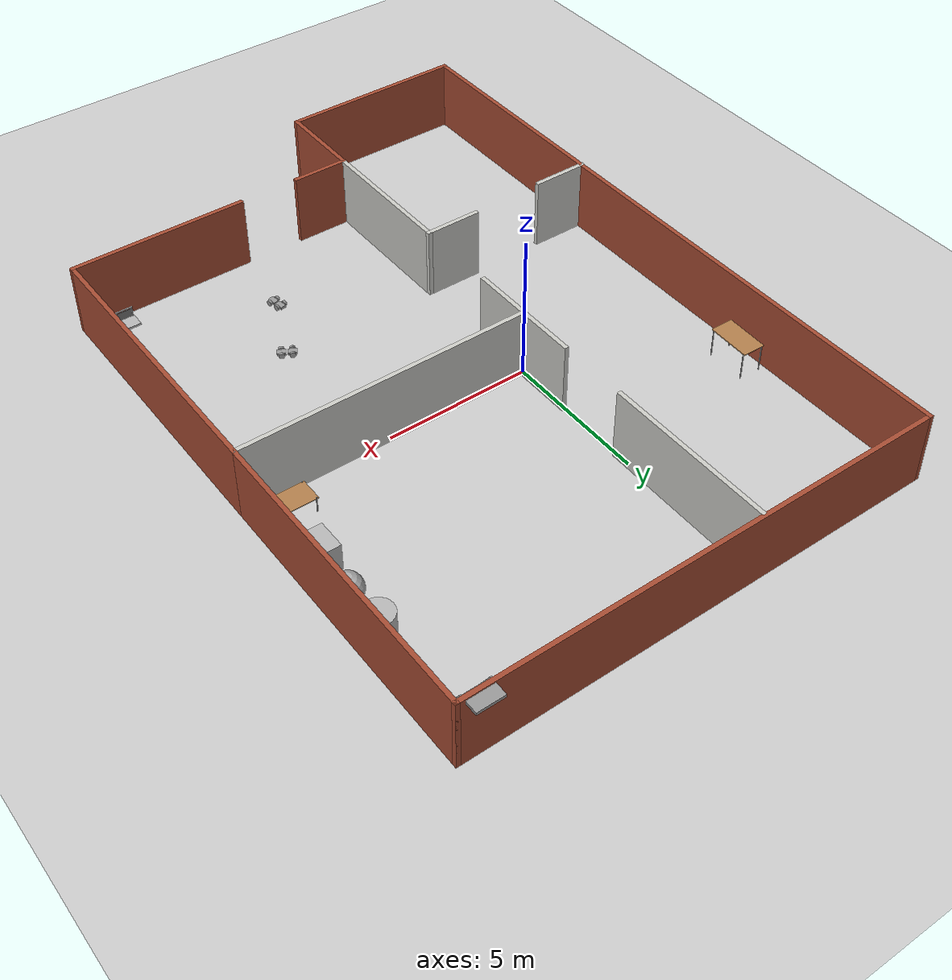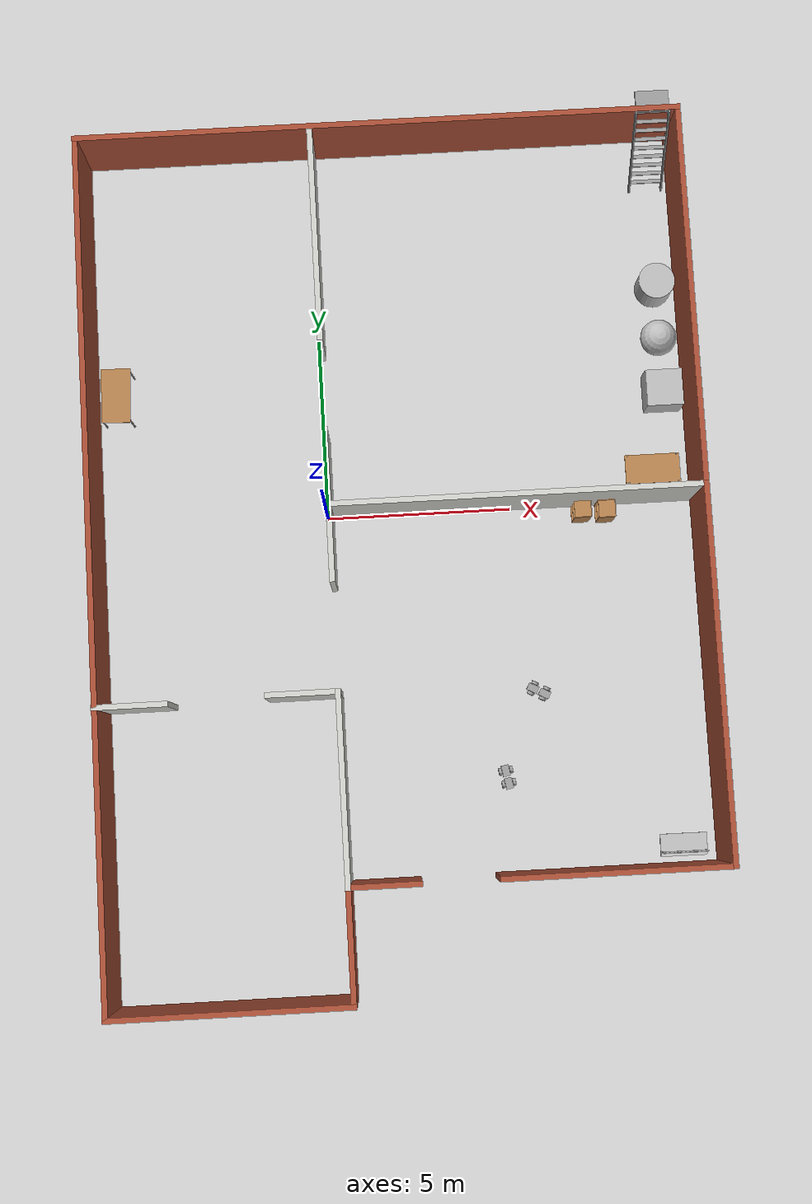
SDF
<sdf version="1.6">
 <world name="default">
  <plugin name="hello" filename="libhello.so"/>
  <light name="sun" type="directional">
   <pose>0 0 10 0 -0 0</pose>
   <diffuse>0.8 0.8 0.8 1</diffuse>
   <specular>0.2 0.2 0.2 1</specular>
   <attenuation>
    <range>1000</range>
    <constant>0.9</constant>
    <linear>0.01</linear>
    <quadratic>0.001</quadratic>
   </attenuation>
   <direction>-0.5 0.1 -0.9</direction>
  </light>
  <model name="ground_plane">
   <static>1</static>
   <link name="link">
    <collision name="collision">
     <geometry><plane><normal>0 0 1</normal><size>100 100</size></plane></geometry>
     <surface><friction><ode><mu>100</mu><mu2>50</mu2></ode></friction></surface>
    </collision>
    <visual name="visual">
     <cast_shadows>0</cast_shadows>
     <geometry><plane><normal>0 0 1</normal><size>100 100</size></plane></geometry>
     <material>
      <script><uri>file://media/materials/scripts/gazebo.material</uri><name>Gazebo/Grey</name></script>
     </material>
    </visual>
   </link>
  </model>
  <gravity>0 0 -9.8</gravity>
  <magnetic_field>6e-06 2.3e-05 -4.2e-05</magnetic_field>
  <atmosphere type="adiabatic"/>
  <physics name="default_physics" default="0" type="ode">
   <max_step_size>0.001</max_step_size>
   <real_time_factor>1</real_time_factor>
   <real_time_update_rate>1000</real_time_update_rate>
  </physics>
  <scene><ambient>0.4 0.4 0.4 1</ambient><background>0.7 0.7 0.7 1</background><shadows>1</shadows></scene>
  <audio><device>default</device></audio>
  <spherical_coordinates>
   <surface_model>EARTH_WGS84</surface_model>
   <latitude_deg>0</latitude_deg>
   <longitude_deg>0</longitude_deg>
   <elevation>0</elevation>
   <heading_deg>0</heading_deg>
  </spherical_coordinates>
  <model name="Building">
   <pose>1.88689 -1.28718 0 0 -0 0</pose>
   <link name="Wall_30">
    <collision name="Wall_30_Collision">
     <geometry><box><size>10.15 0.15 2.5</size></box></geometry>
     <pose>0 0 1.25 0 -0 0</pose>
    </collision>
    <visual name="Wall_30_Visual">
     <pose>0 0 1.25 0 -0 0</pose>
     <geometry><box><size>10.15 0.15 2.5</size></box></geometry>
     <material>
      <script><uri>file://media/materials/scripts/gazebo.material</uri><name>Gazebo/CeilingTiled</name></script>
      <ambient>0.203922 0.396078 0.643137 1</ambient>
     </material>
     <meta><layer>0</layer></meta>
    </visual>
    <pose>3.18412 1.325 0 0 -0 0</pose>
   </link>
   <link name="Wall_34">
    <collision name="Wall_34_Collision">
     <geometry><box><size>10.15 0.15 2.5</size></box></geometry>
     <pose>0 0 1.25 0 -0 0</pose>
    </collision>
    <visual name="Wall_34_Visual">
     <pose>0 0 1.25 0 -0 0</pose>
     <geometry><box><size>10.15 0.15 2.5</size></box></geometry>
     <material>
      <script><uri>file://media/materials/scripts/gazebo.material</uri><name>Gazebo/Bricks</name></script>
      <ambient>1 1 1 1</ambient>
     </material>
     <meta><layer>0</layer></meta>
    </visual>
    <pose>8.18412 -3.675 0 0 -0 -1.5708</pose>
   </link>
   <link name="Wall_36">
    <collision name="Wall_36_Collision">
     <geometry><box><size>6.15 0.15 2.5</size></box></geometry>
     <pose>0 0 1.25 0 -0 0</pose>
    </collision>
    <visual name="Wall_36_Visual">
     <pose>0 0 1.25 0 -0 0</pose>
     <geometry><box><size>6.15 0.15 2.5</size></box></geometry>
     <material>
      <script><uri>file://media/materials/scripts/gazebo.material</uri><name>Gazebo/Bricks</name></script>
      <ambient>1 1 1 1</ambient>
     </material>
     <meta><layer>0</layer></meta>
    </visual>
    <pose>5.18412 -8.675 0 0 -0 3.14159</pose>
   </link>
   <link name="Wall_38">
    <collision name="Wall_38_Collision">
     <geometry><box><size>5.2029 0.15 2.5</size></box></geometry>
     <pose>0 0 1.25 0 -0 0</pose>
    </collision>
    <visual name="Wall_38_Visual">
     <pose>0 0 1.25 0 -0 0</pose>
     <geometry><box><size>5.2029 0.15 2.5</size></box></geometry>
     <material>
      <script><uri>file://media/materials/scripts/gazebo.material</uri><name>Gazebo/CeilingTiled</name></script>
      <ambient>0.203922 0.396078 0.643137 1</ambient>
     </material>
     <meta><layer>0</layer></meta>
    </visual>
    <pose>-1.81588 -6.14855 0 0 -0 1.5708</pose>
   </link>
   <link name="Wall_40">
    <collision name="Wall_40_Collision">
     <geometry><box><size>2 0.15 2.5</size></box></geometry>
     <pose>0 0 1.25 0 -0 0</pose>
    </collision>
    <visual name="Wall_40_Visual">
     <pose>0 0 1.25 0 -0 0</pose>
     <geometry><box><size>2 0.15 2.5</size></box></geometry>
     <material>
      <script><uri>file://media/materials/scripts/gazebo.material</uri><name>Gazebo/Bricks</name></script>
      <ambient>1 1 1 1</ambient>
     </material>
     <meta><layer>0</layer></meta>
    </visual>
    <pose>-0.890877 -8.675 0 0 -0 0</pose>
   </link>
   <link name="Wall_42">
    <collision name="Wall_42_Collision">
     <geometry><box><size>3.15 0.15 2.5</size></box></geometry>
     <pose>0 0 1.25 0 -0 0</pose>
    </collision>
    <visual name="Wall_42_Visual">
     <pose>0 0 1.25 0 -0 0</pose>
     <geometry><box><size>3.15 0.15 2.5</size></box></geometry>
     <material>
      <script><uri>file://media/materials/scripts/gazebo.material</uri><name>Gazebo/Bricks</name></script>
      <ambient>1 1 1 1</ambient>
     </material>
     <meta><layer>0</layer></meta>
    </visual>
    <pose>-1.81588 -10.175 0 0 -0 -1.5708</pose>
   </link>
   <link name="Wall_44">
    <collision name="Wall_44_Collision">
     <geometry><box><size>6.5 0.15 2.5</size></box></geometry>
     <pose>0 0 1.25 0 -0 0</pose>
    </collision>
    <visual name="Wall_44_Visual">
     <pose>0 0 1.25 0 -0 0</pose>
     <geometry><box><size>6.5 0.15 2.5</size></box></geometry>
     <material>
      <script><uri>file://media/materials/scripts/gazebo.material</uri><name>Gazebo/Bricks</name></script>
      <ambient>1 1 1 1</ambient>
     </material>
     <meta><layer>0</layer></meta>
    </visual>
    <pose>-4.99088 -11.675 0 0 -0 3.14159</pose>
   </link>
   <link name="Wall_45">
    <collision name="Wall_45_Collision">
     <geometry><box><size>23.5 0.15 2.5</size></box></geometry>
     <pose>0 0 1.25 0 -0 0</pose>
    </collision>
    <visual name="Wall_45_Visual">
     <pose>0 0 1.25 0 -0 0</pose>
     <geometry><box><size>23.5 0.15 2.5</size></box></geometry>
     <material>
      <script><uri>file://media/materials/scripts/gazebo.material</uri><name>Gazebo/Bricks</name></script>
      <ambient>1 1 1 1</ambient>
     </material>
     <meta><layer>0</layer></meta>
    </visual>
    <pose>-8.16588 0 0 0 -0 1.5708</pose>
   </link>
   <link name="Wall_47">
    <collision name="Wall_47_Collision">
     <geometry><box><size>2.15 0.15 2.5</size></box></geometry>
     <pose>0 0 1.25 0 -0 0</pose>
    </collision>
    <visual name="Wall_47_Visual">
     <pose>0 0 1.25 0 -0 0</pose>
     <geometry><box><size>2.15 0.15 2.5</size></box></geometry>
     <material>
      <script><uri>file://media/materials/scripts/gazebo.material</uri><name>Gazebo/CeilingTiled</name></script>
      <ambient>0.203922 0.396078 0.643137 1</ambient>
     </material>
     <meta><layer>0</layer></meta>
    </visual>
    <pose>-1.81588 0.325 0 0 -0 1.5708</pose>
   </link>
   <link name="Wall_49">
    <collision name="Wall_49_Collision">
     <geometry><box><size>2 0.15 2.5</size></box></geometry>
     <pose>0 0 1.25 0 -0 0</pose>
    </collision>
    <visual name="Wall_49_Visual">
     <pose>0 0 1.25 0 -0 0</pose>
     <geometry><box><size>2 0.15 2.5</size></box></geometry>
     <material>
      <script><uri>file://media/materials/scripts/gazebo.material</uri><name>Gazebo/CeilingTiled</name></script>
      <ambient>0.203922 0.396078 0.643137 1</ambient>
     </material>
     <meta><layer>0</layer></meta>
    </visual>
    <pose>-7.25912 -3.70088 0 0 -0 0</pose>
   </link>
   <link name="Wall_51">
    <collision name="Wall_51_Collision">
     <geometry><box><size>2 0.15 2.5</size></box></geometry>
     <pose>0 0 1.25 0 -0 0</pose>
    </collision>
    <visual name="Wall_51_Visual">
     <pose>0 0 1.25 0 -0 0</pose>
     <geometry><box><size>2 0.15 2.5</size></box></geometry>
     <material>
      <script><uri>file://media/materials/scripts/gazebo.material</uri><name>Gazebo/CeilingTiled</name></script>
      <ambient>0.203922 0.396078 0.643137 1</ambient>
     </material>
     <meta><layer>0</layer></meta>
    </visual>
    <pose>-2.74088 -3.6221 0 0 -0 3.14159</pose>
   </link>
   <link name="Wall_53">
    <collision name="Wall_53_Collision">
     <geometry><box><size>2.15 0.15 2.5</size></box></geometry>
     <pose>0 0 1.25 0 -0 0</pose>
    </collision>
    <visual name="Wall_53_Visual">
     <pose>0 0 1.25 0 -0 0</pose>
     <geometry><box><size>2.15 0.15 2.5</size></box></geometry>
     <material>
      <script><uri>file://media/materials/scripts/gazebo.material</uri><name>Gazebo/CeilingTiled</name></script>
      <ambient>0.203922 0.396078 0.643137 1</ambient>
     </material>
     <meta><layer>0</layer></meta>
    </visual>
    <pose>-1.81588 2.325 0 0 -0 1.5708</pose>
   </link>
   <link name="Wall_55">
    <collision name="Wall_55_Collision">
     <geometry><box><size>16.5 0.15 2.5</size></box></geometry>
     <pose>0 0 1.25 0 -0 0</pose>
    </collision>
    <visual name="Wall_55_Visual">
     <pose>0 0 1.25 0 -0 0</pose>
     <geometry><box><size>16.5 0.15 2.5</size></box></geometry>
     <material>
      <script><uri>file://media/materials/scripts/gazebo.material</uri><name>Gazebo/Bricks</name></script>
      <ambient>1 1 1 1</ambient>
     </material>
     <meta><layer>0</layer></meta>
    </visual>
    <pose>0.009123 11.675 0 0 -0 0</pose>
   </link>
   <link name="Wall_57">
    <collision name="Wall_57_Collision">
     <geometry><box><size>10.5 0.15 2.5</size></box></geometry>
     <pose>0 0 1.25 0 -0 0</pose>
    </collision>
    <visual name="Wall_57_Visual">
     <pose>0 0 1.25 0 -0 0</pose>
     <geometry><box><size>10.5 0.15 2.5</size></box></geometry>
     <material>
      <script><uri>file://media/materials/scripts/gazebo.material</uri><name>Gazebo/Bricks</name></script>
      <ambient>1 1 1 1</ambient>
     </material>
     <meta><layer>0</layer></meta>
    </visual>
    <pose>8.18412 6.5 0 0 -0 1.5708</pose>
   </link>
   <link name="Wall_59">
    <collision name="Wall_59_Collision">
     <geometry><box><size>5.9 0.15 2.5</size></box></geometry>
     <pose>0 0 1.25 0 -0 0</pose>
    </collision>
    <visual name="Wall_59_Visual">
     <pose>0 0 1.25 0 -0 0</pose>
     <geometry><box><size>5.9 0.15 2.5</size></box></geometry>
     <material>
      <script><uri>file://media/materials/scripts/gazebo.material</uri><name>Gazebo/CeilingTiled</name></script>
      <ambient>0.203922 0.396078 0.643137 1</ambient>
     </material>
     <meta><layer>0</layer></meta>
    </visual>
    <pose>-1.81588 8.7 0 0 -0 -1.5708</pose>
   </link>
   <static>1</static>
  </model>
  <model name="ladder_60deg_0rails">
   <static>1</static>
   <link name="step0">
    <pose>0 0.15396 0.266667 0 -0 0</pose>
    <inertial>
     <mass>9.75482</mass>
     <inertia>
      <ixx>0.00957124</ixx>
      <iyy>0.65963</iyy>
      <izz>0.666842</izz>
      <ixy>0</ixy>
      <ixz>0</ixz>
      <iyz>0</iyz>
     </inertia>
    </inertial>
    <collision name="collision"><geometry><box><size>0.9 0.1016 0.0381</size></box></geometry></collision>
    <visual name="visual">
     <geometry><box><size>0.9 0.1016 0.0381</size></box></geometry>
     <material>
      <script><uri>file://media/materials/scripts/gazebo.material</uri><name>Gazebo/Grey</name></script>
     </material>
    </visual>
   </link>
   <link name="step1">
    <pose>0 0.30792 0.533333 0 -0 0</pose>
    <inertial>
     <mass>9.75482</mass>
     <inertia>
      <ixx>0.00957124</ixx>
      <iyy>0.65963</iyy>
      <izz>0.666842</izz>
      <ixy>0</ixy>
      <ixz>0</ixz>
      <iyz>0</iyz>
     </inertia>
    </inertial>
    <collision name="collision"><geometry><box><size>0.9 0.1016 0.0381</size></box></geometry></collision>
    <visual name="visual">
     <geometry><box><size>0.9 0.1016 0.0381</size></box></geometry>
     <material>
      <script><uri>file://media/materials/scripts/gazebo.material</uri><name>Gazebo/Grey</name></script>
     </material>
    </visual>
   </link>
   <link name="step2">
    <pose>0 0.46188 0.8 0 -0 0</pose>
    <inertial>
     <mass>9.75482</mass>
     <inertia>
      <ixx>0.00957124</ixx>
      <iyy>0.65963</iyy>
      <izz>0.666842</izz>
      <ixy>0</ixy>
      <ixz>0</ixz>
      <iyz>0</iyz>
     </inertia>
    </inertial>
    <collision name="collision"><geometry><box><size>0.9 0.1016 0.0381</size></box></geometry></collision>
    <visual name="visual">
     <geometry><box><size>0.9 0.1016 0.0381</size></box></geometry>
     <material>
      <script><uri>file://media/materials/scripts/gazebo.material</uri><name>Gazebo/Grey</name></script>
     </material>
    </visual>
   </link>
   <link name="step3">
    <pose>0 0.61584 1.06667 0 -0 0</pose>
    <inertial>
     <mass>9.75482</mass>
     <inertia>
      <ixx>0.00957124</ixx>
      <iyy>0.65963</iyy>
      <izz>0.666842</izz>
      <ixy>0</ixy>
      <ixz>0</ixz>
      <iyz>0</iyz>
     </inertia>
    </inertial>
    <collision name="collision"><geometry><box><size>0.9 0.1016 0.0381</size></box></geometry></collision>
    <visual name="visual">
     <geometry><box><size>0.9 0.1016 0.0381</size></box></geometry>
     <material>
      <script><uri>file://media/materials/scripts/gazebo.material</uri><name>Gazebo/Grey</name></script>
     </material>
    </visual>
   </link>
   <link name="step4">
    <pose>0 0.7698 1.33333 0 -0 0</pose>
    <inertial>
     <mass>9.75482</mass>
     <inertia>
      <ixx>0.00957124</ixx>
      <iyy>0.65963</iyy>
      <izz>0.666842</izz>
      <ixy>0</ixy>
      <ixz>0</ixz>
      <iyz>0</iyz>
     </inertia>
    </inertial>
    <collision name="collision"><geometry><box><size>0.9 0.1016 0.0381</size></box></geometry></collision>
    <visual name="visual">
     <geometry><box><size>0.9 0.1016 0.0381</size></box></geometry>
     <material>
      <script><uri>file://media/materials/scripts/gazebo.material</uri><name>Gazebo/Grey</name></script>
     </material>
    </visual>
   </link>
   <link name="step5">
    <pose>0 0.92376 1.6 0 -0 0</pose>
    <inertial>
     <mass>9.75482</mass>
     <inertia>
      <ixx>0.00957124</ixx>
      <iyy>0.65963</iyy>
      <izz>0.666842</izz>
      <ixy>0</ixy>
      <ixz>0</ixz>
      <iyz>0</iyz>
     </inertia>
    </inertial>
    <collision name="collision"><geometry><box><size>0.9 0.1016 0.0381</size></box></geometry></collision>
    <visual name="visual">
     <geometry><box><size>0.9 0.1016 0.0381</size></box></geometry>
     <material>
      <script><uri>file://media/materials/scripts/gazebo.material</uri><name>Gazebo/Grey</name></script>
     </material>
    </visual>
   </link>
   <link name="step6">
    <pose>0 1.07772 1.86667 0 -0 0</pose>
    <inertial>
     <mass>9.75482</mass>
     <inertia>
      <ixx>0.00957124</ixx>
      <iyy>0.65963</iyy>
      <izz>0.666842</izz>
      <ixy>0</ixy>
      <ixz>0</ixz>
      <iyz>0</iyz>
     </inertia>
    </inertial>
    <collision name="collision"><geometry><box><size>0.9 0.1016 0.0381</size></box></geometry></collision>
    <visual name="visual">
     <geometry><box><size>0.9 0.1016 0.0381</size></box></geometry>
     <material>
      <script><uri>file://media/materials/scripts/gazebo.material</uri><name>Gazebo/Grey</name></script>
     </material>
    </visual>
   </link>
   <link name="step7">
    <pose>0 1.23168 2.13333 0 -0 0</pose>
    <inertial>
     <mass>9.75482</mass>
     <inertia>
      <ixx>0.00957124</ixx>
      <iyy>0.65963</iyy>
      <izz>0.666842</izz>
      <ixy>0</ixy>
      <ixz>0</ixz>
      <iyz>0</iyz>
     </inertia>
    </inertial>
    <collision name="collision"><geometry><box><size>0.9 0.1016 0.0381</size></box></geometry></collision>
    <visual name="visual">
     <geometry><box><size>0.9 0.1016 0.0381</size></box></geometry>
     <material>
      <script><uri>file://media/materials/scripts/gazebo.material</uri><name>Gazebo/Grey</name></script>
     </material>
    </visual>
   </link>
   <link name="landing">
    <pose>0 1.68564 2.4 0 -0 0</pose>
    <inertial>
     <mass>57.6072</mass>
     <inertia><ixx>1.73518</ixx><iyy>3.89545</iyy><izz>5.6167</izz><ixy>0</ixy><ixz>0</ixz><iyz>0</iyz></inertia>
    </inertial>
    <collision name="collision"><geometry><box><size>0.9 0.6 0.1016</size></box></geometry></collision>
    <visual name="visual">
     <geometry><box><size>0.9 0.6 0.1016</size></box></geometry>
     <material>
      <script><uri>file://media/materials/scripts/gazebo.material</uri><name>Gazebo/Grey</name></script>
     </material>
    </visual>
   </link>
   <link name="left_side_wall">
    <pose>-0.45 0.69282 1.2 1.0472 -0 0</pose>
    <collision name="collision"><geometry><box><size>0.0508 2.85128 0.13</size></box></geometry></collision>
    <visual name="visual">
     <geometry><box><size>0.0508 2.85128 0.13</size></box></geometry>
     <material>
      <script><uri>file://media/materials/scripts/gazebo.material</uri><name>Gazebo/Grey</name></script>
     </material>
    </visual>
   </link>
   <link name="right_side_wall">
    <pose>0.45 0.69282 1.2 1.0472 -0 0</pose>
    <collision name="collision"><geometry><box><size>0.0508 2.85128 0.13</size></box></geometry></collision>
    <visual name="visual">
     <geometry><box><size>0.0508 2.85128 0.13</size></box></geometry>
     <material>
      <script><uri>file://media/materials/scripts/gazebo.material</uri><name>Gazebo/Grey</name></script>
     </material>
    </visual>
   </link>
   <pose>9.39979 8.90239 0 0 -0 0</pose>
  </model>
  <model name="table">
   <static>1</static>
   <link name="link">
    <collision name="surface">
     <pose>0 0 1 0 -0 0</pose>
     <geometry><box><size>1.5 0.8 0.03</size></box></geometry>
     <surface><friction><ode><mu>0.6</mu><mu2>0.6</mu2></ode></friction></surface>
    </collision>
    <visual name="visual1">
     <pose>0 0 1 0 -0 0</pose>
     <geometry><box><size>1.5 0.8 0.03</size></box></geometry>
     <material>
      <script><uri>file://media/materials/scripts/gazebo.material</uri><name>Gazebo/Wood</name></script>
     </material>
    </visual>
    <collision name="front_left_leg">
     <pose>0.68 0.38 0.5 0 -0 0</pose>
     <geometry><cylinder><radius>0.02</radius><length>1</length></cylinder></geometry>
    </collision>
    <visual name="front_left_leg">
     <pose>0.68 0.38 0.5 0 -0 0</pose>
     <geometry><cylinder><radius>0.02</radius><length>1</length></cylinder></geometry>
     <material>
      <script><uri>file://media/materials/scripts/gazebo.material</uri><name>Gazebo/Grey</name></script>
     </material>
    </visual>
    <collision name="front_right_leg">
     <pose>0.68 -0.38 0.5 0 -0 0</pose>
     <geometry><cylinder><radius>0.02</radius><length>1</length></cylinder></geometry>
    </collision>
    <visual name="front_right_leg">
     <pose>0.68 -0.38 0.5 0 -0 0</pose>
     <geometry><cylinder><radius>0.02</radius><length>1</length></cylinder></geometry>
     <material>
      <script><uri>file://media/materials/scripts/gazebo.material</uri><name>Gazebo/Grey</name></script>
     </material>
    </visual>
    <collision name="back_right_leg">
     <pose>-0.68 -0.38 0.5 0 -0 0</pose>
     <geometry><cylinder><radius>0.02</radius><length>1</length></cylinder></geometry>
    </collision>
    <visual name="back_right_leg">
     <pose>-0.68 -0.38 0.5 0 -0 0</pose>
     <geometry><cylinder><radius>0.02</radius><length>1</length></cylinder></geometry>
     <material>
      <script><uri>file://media/materials/scripts/gazebo.material</uri><name>Gazebo/Grey</name></script>
     </material>
    </visual>
    <collision name="back_left_leg">
     <pose>-0.68 0.38 0.5 0 -0 0</pose>
     <geometry><cylinder><radius>0.02</radius><length>1</length></cylinder></geometry>
    </collision>
    <visual name="back_left_leg">
     <pose>-0.68 0.38 0.5 0 -0 0</pose>
     <geometry><cylinder><radius>0.02</radius><length>1</length></cylinder></geometry>
     <material>
      <script><uri>file://media/materials/scripts/gazebo.material</uri><name>Gazebo/Grey</name></script>
     </material>
    </visual>
   </link>
   <pose>-5.62223 3.56497 0 0 0 -1.598</pose>
  </model>
  <model name="cabinet">
   <static>1</static>
   <link name="cabinet_bottom_plate">
    <inertial>
     <pose>0 0 -1 0 -0 0</pose>
     <inertia><ixx>2.05</ixx><ixy>0</ixy><ixz>0</ixz><iyy>2.05</iyy><iyz>0</iyz><izz>2.05</izz></inertia>
     <mass>25</mass>
    </inertial>
    <collision name="cabinet_bottom_plate_geom">
     <pose>0 0 0.01 0 -0 0</pose>
     <geometry><box><size>0.45 0.45 0.02</size></box></geometry>
    </collision>
    <visual name="cabinet_bottom_plate_geom_visual">
     <pose>0 0 0.01 0 -0 0</pose>
     <geometry><box><size>0.45 0.45 0.02</size></box></geometry>
     <material>
      <script><uri>file://media/materials/scripts/gazebo.material</uri><name>Gazebo/Wood</name></script>
     </material>
    </visual>
    <collision name="cabinet_bottom_plate_geom_cabinet_back_plate">
     <pose>0.235 0 0.51 0 -0 0</pose>
     <geometry><box><size>0.02 0.45 1.02</size></box></geometry>
    </collision>
    <visual name="cabinet_bottom_plate_geom_cabinet_back_plate_visual">
     <pose>0.235 0 0.51 0 -0 0</pose>
     <geometry><box><size>0.02 0.45 1.02</size></box></geometry>
     <material>
      <script><uri>file://media/materials/scripts/gazebo.material</uri><name>Gazebo/Wood</name></script>
     </material>
    </visual>
    <collision name="cabinet_bottom_plate_geom_cabinet_left_plate">
     <pose>0 0.235 0.51 0 -0 0</pose>
     <geometry><box><size>0.45 0.02 1.02</size></box></geometry>
    </collision>
    <visual name="cabinet_bottom_plate_geom_cabinet_left_plate_visual">
     <pose>0 0.235 0.51 0 -0 0</pose>
     <geometry><box><size>0.45 0.02 1.02</size></box></geometry>
     <material>
      <script><uri>file://media/materials/scripts/gazebo.material</uri><name>Gazebo/Wood</name></script>
     </material>
    </visual>
    <collision name="cabinet_bottom_plate_geom_cabinet_middle_plate">
     <pose>0 0 0.51 0 -0 0</pose>
     <geometry><box><size>0.45 0.45 0.02</size></box></geometry>
    </collision>
    <visual name="cabinet_bottom_plate_geom_cabinet_middle_plate_visual">
     <pose>0 0 0.51 0 -0 0</pose>
     <geometry><box><size>0.45 0.45 0.02</size></box></geometry>
     <material>
      <script><uri>file://media/materials/scripts/gazebo.material</uri><name>Gazebo/Wood</name></script>
     </material>
    </visual>
    <collision name="cabinet_bottom_plate_geom_cabinet_right_plate">
     <pose>0 -0.235 0.51 0 -0 0</pose>
     <geometry><box><size>0.45 0.02 1.02</size></box></geometry>
    </collision>
    <visual name="cabinet_bottom_plate_geom_cabinet_right_plate_visual">
     <pose>0 -0.235 0.51 0 -0 0</pose>
     <geometry><box><size>0.45 0.02 1.02</size></box></geometry>
     <material>
      <script><uri>file://media/materials/scripts/gazebo.material</uri><name>Gazebo/Wood</name></script>
     </material>
    </visual>
    <collision name="cabinet_bottom_plate_geom_cabinet_top_plate">
     <pose>0 0 1.01 0 -0 0</pose>
     <geometry><box><size>0.45 0.45 0.02</size></box></geometry>
    </collision>
    <visual name="cabinet_bottom_plate_geom_cabinet_top_plate_visual">
     <pose>0 0 1.01 0 -0 0</pose>
     <geometry><box><size>0.45 0.45 0.02</size></box></geometry>
     <material>
      <script><uri>file://media/materials/scripts/gazebo.material</uri><name>Gazebo/Wood</name></script>
     </material>
    </visual>
   </link>
   <pose>7.57445 -0.283027 0 0 -0 0</pose>
  </model>
  <model name="minitable">
   <link name="link">
    <inertial>
     <mass>1</mass>
     <inertia><ixx>1</ixx><ixy>0</ixy><ixz>0</ixz><iyy>1</iyy><iyz>0</iyz><izz>1</izz></inertia>
    </inertial>
    <visual name="visual1">
     <pose>0 0 0.5 0 -0 0</pose>
     <geometry><box><size>1.5 0.8 0.03</size></box></geometry>
     <material>
      <script><uri>file://media/materials/scripts/gazebo.material</uri><name>Gazebo/Wood</name></script>
      <shader type="pixel"><normal_map>__default__</normal_map></shader>
      <ambient>1 1 1 1</ambient>
      <diffuse>1 1 1 1</diffuse>
      <specular>0.2 0.2 0.2 1</specular>
      <emissive>0 0 0 1</emissive>
     </material>
    </visual>
    <visual name="front_left_leg">
     <pose>0.68 0.38 0.05 0 -0 0</pose>
     <geometry><cylinder><radius>0.02</radius><length>1</length></cylinder></geometry>
     <material>
      <script><uri>file://media/materials/scripts/gazebo.material</uri><name>Gazebo/Grey</name></script>
      <shader type="pixel"><normal_map>__default__</normal_map></shader>
      <ambient>0.3 0.3 0.3 1</ambient>
      <diffuse>0.7 0.7 0.7 1</diffuse>
      <specular>0.01 0.01 0.01 1</specular>
      <emissive>0 0 0 1</emissive>
     </material>
    </visual>
    <visual name="front_right_leg">
     <pose>0.68 -0.38 0.05 0 -0 0</pose>
     <geometry><cylinder><radius>0.02</radius><length>1</length></cylinder></geometry>
     <material>
      <script><uri>file://media/materials/scripts/gazebo.material</uri><name>Gazebo/Grey</name></script>
      <shader type="pixel"><normal_map>__default__</normal_map></shader>
      <ambient>0.3 0.3 0.3 1</ambient>
      <diffuse>0.7 0.7 0.7 1</diffuse>
      <specular>0.01 0.01 0.01 1</specular>
      <emissive>0 0 0 1</emissive>
     </material>
    </visual>
    <visual name="back_right_leg">
     <pose>-0.68 -0.38 0.05 0 -0 0</pose>
     <geometry><cylinder><radius>0.02</radius><length>1</length></cylinder></geometry>
     <material>
      <script><uri>file://media/materials/scripts/gazebo.material</uri><name>Gazebo/Grey</name></script>
      <shader type="pixel"><normal_map>__default__</normal_map></shader>
      <ambient>0.3 0.3 0.3 1</ambient>
      <diffuse>0.7 0.7 0.7 1</diffuse>
      <specular>0.01 0.01 0.01 1</specular>
      <emissive>0 0 0 1</emissive>
     </material>
    </visual>
    <visual name="back_left_leg">
     <pose>-0.68 0.38 0.05 0 -0 0</pose>
     <geometry><cylinder><radius>0.02</radius><length>1</length></cylinder></geometry>
     <material>
      <script><uri>file://media/materials/scripts/gazebo.material</uri><name>Gazebo/Grey</name></script>
      <shader type="pixel"><normal_map>__default__</normal_map></shader>
      <ambient>0.3 0.3 0.3 1</ambient>
      <diffuse>0.7 0.7 0.7 1</diffuse>
      <specular>0.01 0.01 0.01 1</specular>
      <emissive>0 0 0 1</emissive>
     </material>
    </visual>
    <collision name="surface">
     <pose>0 0 0.5 0 -0 0</pose>
     <geometry><box><size>1.5 0.8 0.03</size></box></geometry>
     <surface>
      <friction>
       <ode><mu>0.6</mu><mu2>0.6</mu2><fdir1>0 0 0</fdir1><slip1>0</slip1><slip2>0</slip2></ode>
       <torsional>
        <coefficient>1</coefficient>
        <patch_radius>0</patch_radius>
        <surface_radius>0</surface_radius>
        <use_patch_radius>1</use_patch_radius>
        <ode><slip>0</slip></ode>
       </torsional>
      </friction>
      <bounce><restitution_coefficient>0</restitution_coefficient><threshold>1e+06</threshold></bounce>
      <contact>
       <collide_without_contact>0</collide_without_contact>
       <collide_without_contact_bitmask>1</collide_without_contact_bitmask>
       <collide_bitmask>1</collide_bitmask>
       <ode>
        <soft_cfm>0</soft_cfm>
        <soft_erp>0.2</soft_erp>
        <kp>1e+13</kp>
        <kd>1</kd>
        <max_vel>0.01</max_vel>
        <min_depth>0</min_depth>
       </ode>
       <bullet>
        <split_impulse>1</split_impulse>
        <split_impulse_penetration_threshold>-0.01</split_impulse_penetration_threshold>
        <soft_cfm>0</soft_cfm>
        <soft_erp>0.2</soft_erp>
        <kp>1e+13</kp>
        <kd>1</kd>
       </bullet>
      </contact>
     </surface>
    </collision>
    <collision name="front_left_leg">
     <pose>0.68 0.38 0.05 0 -0 0</pose>
     <geometry><cylinder><radius>0.02</radius><length>1</length></cylinder></geometry>
     <surface>
      <friction>
       <ode><mu>1</mu><mu2>1</mu2><fdir1>0 0 0</fdir1><slip1>0</slip1><slip2>0</slip2></ode>
       <torsional>
        <coefficient>1</coefficient>
        <patch_radius>0</patch_radius>
        <surface_radius>0</surface_radius>
        <use_patch_radius>1</use_patch_radius>
        <ode><slip>0</slip></ode>
       </torsional>
      </friction>
      <bounce><restitution_coefficient>0</restitution_coefficient><threshold>1e+06</threshold></bounce>
      <contact>
       <collide_without_contact>0</collide_without_contact>
       <collide_without_contact_bitmask>1</collide_without_contact_bitmask>
       <collide_bitmask>1</collide_bitmask>
       <ode>
        <soft_cfm>0</soft_cfm>
        <soft_erp>0.2</soft_erp>
        <kp>1e+13</kp>
        <kd>1</kd>
        <max_vel>0.01</max_vel>
        <min_depth>0</min_depth>
       </ode>
       <bullet>
        <split_impulse>1</split_impulse>
        <split_impulse_penetration_threshold>-0.01</split_impulse_penetration_threshold>
        <soft_cfm>0</soft_cfm>
        <soft_erp>0.2</soft_erp>
        <kp>1e+13</kp>
        <kd>1</kd>
       </bullet>
      </contact>
     </surface>
    </collision>
    <collision name="front_right_leg">
     <pose>0.68 -0.38 0.05 0 -0 0</pose>
     <geometry><cylinder><radius>0.02</radius><length>1</length></cylinder></geometry>
     <surface>
      <friction>
       <ode><mu>1</mu><mu2>1</mu2><fdir1>0 0 0</fdir1><slip1>0</slip1><slip2>0</slip2></ode>
       <torsional>
        <coefficient>1</coefficient>
        <patch_radius>0</patch_radius>
        <surface_radius>0</surface_radius>
        <use_patch_radius>1</use_patch_radius>
        <ode><slip>0</slip></ode>
       </torsional>
      </friction>
      <bounce><restitution_coefficient>0</restitution_coefficient><threshold>1e+06</threshold></bounce>
      <contact>
       <collide_without_contact>0</collide_without_contact>
       <collide_without_contact_bitmask>1</collide_without_contact_bitmask>
       <collide_bitmask>1</collide_bitmask>
       <ode>
        <soft_cfm>0</soft_cfm>
        <soft_erp>0.2</soft_erp>
        <kp>1e+13</kp>
        <kd>1</kd>
        <max_vel>0.01</max_vel>
        <min_depth>0</min_depth>
       </ode>
       <bullet>
        <split_impulse>1</split_impulse>
        <split_impulse_penetration_threshold>-0.01</split_impulse_penetration_threshold>
        <soft_cfm>0</soft_cfm>
        <soft_erp>0.2</soft_erp>
        <kp>1e+13</kp>
        <kd>1</kd>
       </bullet>
      </contact>
     </surface>
    </collision>
    <collision name="back_right_leg">
     <pose>-0.68 -0.38 0.05 0 -0 0</pose>
     <geometry><cylinder><radius>0.02</radius><length>1</length></cylinder></geometry>
     <surface>
      <friction>
       <ode><mu>1</mu><mu2>1</mu2><fdir1>0 0 0</fdir1><slip1>0</slip1><slip2>0</slip2></ode>
       <torsional>
        <coefficient>1</coefficient>
        <patch_radius>0</patch_radius>
        <surface_radius>0</surface_radius>
        <use_patch_radius>1</use_patch_radius>
        <ode><slip>0</slip></ode>
       </torsional>
      </friction>
      <bounce><restitution_coefficient>0</restitution_coefficient><threshold>1e+06</threshold></bounce>
      <contact>
       <collide_without_contact>0</collide_without_contact>
       <collide_without_contact_bitmask>1</collide_without_contact_bitmask>
       <collide_bitmask>1</collide_bitmask>
       <ode>
        <soft_cfm>0</soft_cfm>
        <soft_erp>0.2</soft_erp>
        <kp>1e+13</kp>
        <kd>1</kd>
        <max_vel>0.01</max_vel>
        <min_depth>0</min_depth>
       </ode>
       <bullet>
        <split_impulse>1</split_impulse>
        <split_impulse_penetration_threshold>-0.01</split_impulse_penetration_threshold>
        <soft_cfm>0</soft_cfm>
        <soft_erp>0.2</soft_erp>
        <kp>1e+13</kp>
        <kd>1</kd>
       </bullet>
      </contact>
     </surface>
    </collision>
    <collision name="back_left_leg">
     <pose>-0.68 0.38 0.05 0 -0 0</pose>
     <geometry><cylinder><radius>0.02</radius><length>1</length></cylinder></geometry>
     <surface>
      <friction>
       <ode><mu>1</mu><mu2>1</mu2><fdir1>0 0 0</fdir1><slip1>0</slip1><slip2>0</slip2></ode>
       <torsional>
        <coefficient>1</coefficient>
        <patch_radius>0</patch_radius>
        <surface_radius>0</surface_radius>
        <use_patch_radius>1</use_patch_radius>
        <ode><slip>0</slip></ode>
       </torsional>
      </friction>
      <bounce><restitution_coefficient>0</restitution_coefficient><threshold>1e+06</threshold></bounce>
      <contact>
       <collide_without_contact>0</collide_without_contact>
       <collide_without_contact_bitmask>1</collide_without_contact_bitmask>
       <collide_bitmask>1</collide_bitmask>
       <ode>
        <soft_cfm>0</soft_cfm>
        <soft_erp>0.2</soft_erp>
        <kp>1e+13</kp>
        <kd>1</kd>
        <max_vel>0.01</max_vel>
        <min_depth>0</min_depth>
       </ode>
       <bullet>
        <split_impulse>1</split_impulse>
        <split_impulse_penetration_threshold>-0.01</split_impulse_penetration_threshold>
        <soft_cfm>0</soft_cfm>
        <soft_erp>0.2</soft_erp>
        <kp>1e+13</kp>
        <kd>1</kd>
       </bullet>
      </contact>
     </surface>
    </collision>
   </link>
   <static>1</static>
   <pose>8.96989 0.826322 0 0 -0 0</pose>
  </model>
  <model name="textured_shapes">
   <pose>9.39171 4.48804 0.5 0 -0 0</pose>
   <link name="box">
    <pose>0 -1.5 0 0 -0 0</pose>
    <collision name="collision"><geometry><box><size>1 1 1</size></box></geometry></collision>
    <visual name="visual">
     <geometry><box><size>1 1 1</size></box></geometry>
     <material>
      <script>
       <uri>model://textured_shapes/materials/scripts</uri>
       <uri>model://textured_shapes/materials/textures</uri>
       <name>TexturedShape/Squares</name>
      </script>
     </material>
    </visual>
    <inertial>
     <inertia><ixx>1</ixx><ixy>0</ixy><ixz>0</ixz><iyy>1</iyy><iyz>0</iyz><izz>1</izz></inertia>
     <mass>1</mass>
    </inertial>
   </link>
   <link name="sphere">
    <collision name="collision"><geometry><sphere><radius>0.5</radius></sphere></geometry></collision>
    <visual name="visual">
     <geometry><sphere><radius>0.5</radius></sphere></geometry>
     <material>
      <script>
       <uri>model://textured_shapes/materials/scripts</uri>
       <uri>model://textured_shapes/materials/textures</uri>
       <name>TexturedShape/Squares</name>
      </script>
     </material>
    </visual>
    <inertial>
     <inertia><ixx>1</ixx><ixy>0</ixy><ixz>0</ixz><iyy>1</iyy><iyz>0</iyz><izz>1</izz></inertia>
     <mass>1</mass>
    </inertial>
   </link>
   <link name="cylinder">
    <pose>0 1.5 0 0 -0 0</pose>
    <collision name="collision">
     <geometry><cylinder><radius>0.5</radius><length>1</length></cylinder></geometry>
    </collision>
    <visual name="visual">
     <geometry><cylinder><radius>0.5</radius><length>1</length></cylinder></geometry>
     <material>
      <script>
       <uri>model://textured_shapes/materials/scripts</uri>
       <uri>model://textured_shapes/materials/textures</uri>
       <name>TexturedShape/Squares</name>
      </script>
     </material>
    </visual>
    <inertial>
     <inertia><ixx>1</ixx><ixy>0</ixy><ixz>0</ixz><iyy>1</iyy><iyz>0</iyz><izz>1</izz></inertia>
     <mass>1</mass>
    </inertial>
   </link>
  </model>
  <model name="cabinet_0">
   <static>1</static>
   <link name="cabinet_bottom_plate">
    <inertial>
     <pose>0 0 -1 0 -0 0</pose>
     <inertia><ixx>2.05</ixx><ixy>0</ixy><ixz>0</ixz><iyy>2.05</iyy><iyz>0</iyz><izz>2.05</izz></inertia>
     <mass>25</mass>
    </inertial>
    <collision name="cabinet_bottom_plate_geom">
     <pose>0 0 0.01 0 -0 0</pose>
     <geometry><box><size>0.45 0.45 0.02</size></box></geometry>
    </collision>
    <visual name="cabinet_bottom_plate_geom_visual">
     <pose>0 0 0.01 0 -0 0</pose>
     <geometry><box><size>0.45 0.45 0.02</size></box></geometry>
     <material>
      <script><uri>file://media/materials/scripts/gazebo.material</uri><name>Gazebo/Wood</name></script>
     </material>
    </visual>
    <collision name="cabinet_bottom_plate_geom_cabinet_back_plate">
     <pose>0.235 0 0.51 0 -0 0</pose>
     <geometry><box><size>0.02 0.45 1.02</size></box></geometry>
    </collision>
    <visual name="cabinet_bottom_plate_geom_cabinet_back_plate_visual">
     <pose>0.235 0 0.51 0 -0 0</pose>
     <geometry><box><size>0.02 0.45 1.02</size></box></geometry>
     <material>
      <script><uri>file://media/materials/scripts/gazebo.material</uri><name>Gazebo/Wood</name></script>
     </material>
    </visual>
    <collision name="cabinet_bottom_plate_geom_cabinet_left_plate">
     <pose>0 0.235 0.51 0 -0 0</pose>
     <geometry><box><size>0.45 0.02 1.02</size></box></geometry>
    </collision>
    <visual name="cabinet_bottom_plate_geom_cabinet_left_plate_visual">
     <pose>0 0.235 0.51 0 -0 0</pose>
     <geometry><box><size>0.45 0.02 1.02</size></box></geometry>
     <material>
      <script><uri>file://media/materials/scripts/gazebo.material</uri><name>Gazebo/Wood</name></script>
     </material>
    </visual>
    <collision name="cabinet_bottom_plate_geom_cabinet_middle_plate">
     <pose>0 0 0.51 0 -0 0</pose>
     <geometry><box><size>0.45 0.45 0.02</size></box></geometry>
    </collision>
    <visual name="cabinet_bottom_plate_geom_cabinet_middle_plate_visual">
     <pose>0 0 0.51 0 -0 0</pose>
     <geometry><box><size>0.45 0.45 0.02</size></box></geometry>
     <material>
      <script><uri>file://media/materials/scripts/gazebo.material</uri><name>Gazebo/Wood</name></script>
     </material>
    </visual>
    <collision name="cabinet_bottom_plate_geom_cabinet_right_plate">
     <pose>0 -0.235 0.51 0 -0 0</pose>
     <geometry><box><size>0.45 0.02 1.02</size></box></geometry>
    </collision>
    <visual name="cabinet_bottom_plate_geom_cabinet_right_plate_visual">
     <pose>0 -0.235 0.51 0 -0 0</pose>
     <geometry><box><size>0.45 0.02 1.02</size></box></geometry>
     <material>
      <script><uri>file://media/materials/scripts/gazebo.material</uri><name>Gazebo/Wood</name></script>
     </material>
    </visual>
    <collision name="cabinet_bottom_plate_geom_cabinet_top_plate">
     <pose>0 0 1.01 0 -0 0</pose>
     <geometry><box><size>0.45 0.45 0.02</size></box></geometry>
    </collision>
    <visual name="cabinet_bottom_plate_geom_cabinet_top_plate_visual">
     <pose>0 0 1.01 0 -0 0</pose>
     <geometry><box><size>0.45 0.45 0.02</size></box></geometry>
     <material>
      <script><uri>file://media/materials/scripts/gazebo.material</uri><name>Gazebo/Wood</name></script>
     </material>
    </visual>
   </link>
   <pose>6.91797 -0.248257 0 0 -0 0</pose>
  </model>
  <model name="frc2016_lowbar">
   <link name="base">
    <inertial>
     <mass>50</mass>
     <inertia>
      <ixx>0.035543</ixx>
      <ixy>0</ixy>
      <ixz>0</ixz>
      <iyy>0.134412</iyy>
      <iyz>0</iyz>
      <izz>0.165376</izz>
     </inertia>
    </inertial>
    <visual name="platform">
     <pose>0 0 0.039065 0 -0 0</pose>
     <geometry><box><size>1.26 0.5996 0.07813</size></box></geometry>
    </visual>
    <collision name="platform">
     <pose>0 0 0.039065 0 -0 0</pose>
     <geometry><box><size>1.27 0.6096 0.07813</size></box></geometry>
    </collision>
    <visual name="right_column">
     <pose>-0.57845 -0.18464 0.26863 0 -0 0</pose>
     <geometry><cylinder><radius>0.0254</radius><length>0.381</length></cylinder></geometry>
    </visual>
    <collision name="right_column">
     <pose>-0.57845 -0.18464 0.26863 0 -0 0</pose>
     <geometry><cylinder><radius>0.0254</radius><length>0.381</length></cylinder></geometry>
    </collision>
    <visual name="left_column">
     <pose>0.57845 -0.18464 0.26863 0 -0 0</pose>
     <geometry><cylinder><radius>0.0254</radius><length>0.381</length></cylinder></geometry>
    </visual>
    <collision name="left_column">
     <pose>0.57845 -0.18464 0.26863 0 -0 0</pose>
     <geometry><cylinder><radius>0.0254</radius><length>0.381</length></cylinder></geometry>
    </collision>
    <visual name="horizontal">
     <pose>0 -0.18464 0.43556 0 1.5707 0</pose>
     <geometry><cylinder><radius>0.0254</radius><length>1.2018</length></cylinder></geometry>
    </visual>
    <collision name="horizontal">
     <pose>0 -0.18464 0.43556 0 1.5707 0</pose>
     <geometry><cylinder><radius>0.0254</radius><length>1.2018</length></cylinder></geometry>
    </collision>
   </link>
   <link name="wall">
    <pose>0 -0.1778 0.24323 0 -0 0</pose>
    <inertial>
     <mass>1</mass>
     <inertia>
      <ixx>0.00774528</ixx>
      <ixy>0</ixy>
      <ixz>0</ixz>
      <iyy>0.116613</iyy>
      <iyz>0</iyz>
      <izz>0.108874</izz>
     </inertia>
    </inertial>
    <visual name="visual">
     <geometry><box><size>1.1176 0.00635 0.3</size></box></geometry>
     <material><ambient>0.46 0.46 0.46 1</ambient><diffuse>0.46 0.46 0.46 1</diffuse></material>
    </visual>
    <collision name="collision"><geometry><box><size>1.143 0.00635 0.3</size></box></geometry></collision>
   </link>
   <joint name="bar_joint" type="revolute">
    <pose>0 0 0.36378 0 -0 0</pose>
    <parent>base</parent>
    <child>wall</child>
    <axis>
     <xyz>1 0 0</xyz>
     <limit><lower>-1.5707</lower><upper>1.5707</upper></limit>
     <use_parent_model_frame>0</use_parent_model_frame>
     <dynamics><spring_reference>0</spring_reference><spring_stiffness>0</spring_stiffness></dynamics>
    </axis>
   </joint>
   <pose>9.1262 -9.42422 -0.000101 0 -0.000159 -0.00457</pose>
  </model>
  <model name="ackerDrive">
   <link name="link_0">
    <inertial>
     <mass>1</mass>
     <inertia>
      <ixx>0.166667</ixx>
      <ixy>0</ixy>
      <ixz>0</ixz>
      <iyy>0.166667</iyy>
      <iyz>0</iyz>
      <izz>0.166667</izz>
     </inertia>
    </inertial>
    <self_collide>1</self_collide>
    <visual name="visual">
     <geometry><box><size>0.3 0.2 0.1</size></box></geometry>
     <material>
      <lighting>1</lighting>
      <script><uri>file://media/materials/scripts/gazebo.material</uri><name>Gazebo/Grey</name></script>
      <shader type="vertex"><normal_map>__default__</normal_map></shader>
      <ambient>0.3 0.3 0.3 1</ambient>
      <diffuse>0.7 0.7 0.7 1</diffuse>
      <specular>0.01 0.01 0.01 1</specular>
      <emissive>0 0 0 1</emissive>
     </material>
    </visual>
    <collision name="collision">
     <geometry><box><size>0.3 0.2 0.1</size></box></geometry>
     <surface>
      <friction>
       <ode><mu>1</mu><mu2>1</mu2><fdir1>0 0 0</fdir1><slip1>0</slip1><slip2>0</slip2></ode>
       <torsional>
        <coefficient>1</coefficient>
        <patch_radius>0</patch_radius>
        <surface_radius>0</surface_radius>
        <use_patch_radius>1</use_patch_radius>
        <ode><slip>0</slip></ode>
       </torsional>
      </friction>
      <bounce><restitution_coefficient>0</restitution_coefficient><threshold>1e+06</threshold></bounce>
      <contact>
       <collide_without_contact>0</collide_without_contact>
       <collide_without_contact_bitmask>1</collide_without_contact_bitmask>
       <collide_bitmask>1</collide_bitmask>
       <ode>
        <soft_cfm>0</soft_cfm>
        <soft_erp>0.2</soft_erp>
        <kp>1e+13</kp>
        <kd>1</kd>
        <max_vel>0.01</max_vel>
        <min_depth>0</min_depth>
       </ode>
       <bullet>
        <split_impulse>1</split_impulse>
        <split_impulse_penetration_threshold>-0.01</split_impulse_penetration_threshold>
        <soft_cfm>0</soft_cfm>
        <soft_erp>0.2</soft_erp>
        <kp>1e+13</kp>
        <kd>1</kd>
       </bullet>
      </contact>
     </surface>
    </collision>
   </link>
   <link name="link_0_clone">
    <inertial>
     <mass>1</mass>
     <inertia>
      <ixx>0.166667</ixx>
      <ixy>0</ixy>
      <ixz>0</ixz>
      <iyy>0.166667</iyy>
      <iyz>0</iyz>
      <izz>0.166667</izz>
     </inertia>
    </inertial>
    <pose>0.35 0 0 0 -0 0</pose>
    <self_collide>1</self_collide>
    <visual name="visual">
     <geometry><box><size>0.3 0.2 0.1</size></box></geometry>
     <material>
      <lighting>1</lighting>
      <script><uri>file://media/materials/scripts/gazebo.material</uri><name>Gazebo/Grey</name></script>
      <shader type="vertex"><normal_map>__default__</normal_map></shader>
      <ambient>0.3 0.3 0.3 1</ambient>
      <diffuse>0.7 0.7 0.7 1</diffuse>
      <specular>0.01 0.01 0.01 1</specular>
      <emissive>0 0 0 1</emissive>
     </material>
    </visual>
    <collision name="collision">
     <geometry><box><size>0.3 0.2 0.1</size></box></geometry>
     <surface>
      <friction>
       <ode><mu>1</mu><mu2>1</mu2><fdir1>0 0 0</fdir1><slip1>0</slip1><slip2>0</slip2></ode>
       <torsional>
        <coefficient>1</coefficient>
        <patch_radius>0</patch_radius>
        <surface_radius>0</surface_radius>
        <use_patch_radius>1</use_patch_radius>
        <ode><slip>0</slip></ode>
       </torsional>
      </friction>
      <bounce><restitution_coefficient>0</restitution_coefficient><threshold>1e+06</threshold></bounce>
      <contact>
       <collide_without_contact>0</collide_without_contact>
       <collide_without_contact_bitmask>1</collide_without_contact_bitmask>
       <collide_bitmask>1</collide_bitmask>
       <ode>
        <soft_cfm>0</soft_cfm>
        <soft_erp>0.2</soft_erp>
        <kp>1e+13</kp>
        <kd>1</kd>
        <max_vel>0.01</max_vel>
        <min_depth>0</min_depth>
       </ode>
       <bullet>
        <split_impulse>1</split_impulse>
        <split_impulse_penetration_threshold>-0.01</split_impulse_penetration_threshold>
        <soft_cfm>0</soft_cfm>
        <soft_erp>0.2</soft_erp>
        <kp>1e+13</kp>
        <kd>1</kd>
       </bullet>
      </contact>
     </surface>
    </collision>
   </link>
   <link name="link_1">
    <inertial>
     <mass>1</mass>
     <inertia><ixx>0.145833</ixx><ixy>0</ixy><ixz>0</ixz><iyy>0.145833</iyy><iyz>0</iyz><izz>0.125</izz></inertia>
    </inertial>
    <pose>-0 -0.15 -0 1.57 -0 0</pose>
    <self_collide>1</self_collide>
    <visual name="visual">
     <geometry><cylinder><radius>0.1</radius><length>0.08</length></cylinder></geometry>
     <material>
      <lighting>1</lighting>
      <script><uri>file://media/materials/scripts/gazebo.material</uri><name>Gazebo/Grey</name></script>
      <shader type="vertex"><normal_map>__default__</normal_map></shader>
      <ambient>0.3 0.3 0.3 1</ambient>
      <diffuse>0.7 0.7 0.7 1</diffuse>
      <specular>0.01 0.01 0.01 1</specular>
      <emissive>0 0 0 1</emissive>
     </material>
    </visual>
    <collision name="collision">
     <geometry><cylinder><radius>0.1</radius><length>0.08</length></cylinder></geometry>
     <surface>
      <friction>
       <ode><mu>1</mu><mu2>1</mu2><fdir1>0 0 0</fdir1><slip1>0</slip1><slip2>0</slip2></ode>
       <torsional>
        <coefficient>1</coefficient>
        <patch_radius>0</patch_radius>
        <surface_radius>0</surface_radius>
        <use_patch_radius>1</use_patch_radius>
        <ode><slip>0</slip></ode>
       </torsional>
      </friction>
      <bounce><restitution_coefficient>0</restitution_coefficient><threshold>1e+06</threshold></bounce>
      <contact>
       <collide_without_contact>0</collide_without_contact>
       <collide_without_contact_bitmask>1</collide_without_contact_bitmask>
       <collide_bitmask>1</collide_bitmask>
       <ode>
        <soft_cfm>0</soft_cfm>
        <soft_erp>0.2</soft_erp>
        <kp>1e+13</kp>
        <kd>1</kd>
        <max_vel>0.01</max_vel>
        <min_depth>0</min_depth>
       </ode>
       <bullet>
        <split_impulse>1</split_impulse>
        <split_impulse_penetration_threshold>-0.01</split_impulse_penetration_threshold>
        <soft_cfm>0</soft_cfm>
        <soft_erp>0.2</soft_erp>
        <kp>1e+13</kp>
        <kd>1</kd>
       </bullet>
      </contact>
     </surface>
    </collision>
   </link>
   <link name="link_1_clone">
    <inertial>
     <mass>1</mass>
     <inertia><ixx>0.145833</ixx><ixy>0</ixy><ixz>0</ixz><iyy>0.145833</iyy><iyz>0</iyz><izz>0.125</izz></inertia>
    </inertial>
    <pose>0 0.15 0 1.57 -0 0</pose>
    <self_collide>1</self_collide>
    <visual name="visual">
     <geometry><cylinder><radius>0.1</radius><length>0.08</length></cylinder></geometry>
     <material>
      <lighting>1</lighting>
      <script><uri>file://media/materials/scripts/gazebo.material</uri><name>Gazebo/Grey</name></script>
      <shader type="vertex"><normal_map>__default__</normal_map></shader>
      <ambient>0.3 0.3 0.3 1</ambient>
      <diffuse>0.7 0.7 0.7 1</diffuse>
      <specular>0.01 0.01 0.01 1</specular>
      <emissive>0 0 0 1</emissive>
     </material>
    </visual>
    <collision name="collision">
     <geometry><cylinder><radius>0.1</radius><length>0.08</length></cylinder></geometry>
     <surface>
      <friction>
       <ode><mu>0.98</mu><mu2>1</mu2><fdir1>0 0 0</fdir1><slip1>0</slip1><slip2>0</slip2></ode>
       <torsional>
        <coefficient>1</coefficient>
        <patch_radius>0</patch_radius>
        <surface_radius>0</surface_radius>
        <use_patch_radius>1</use_patch_radius>
        <ode><slip>0</slip></ode>
       </torsional>
      </friction>
      <bounce><restitution_coefficient>0</restitution_coefficient><threshold>1e+06</threshold></bounce>
      <contact>
       <collide_without_contact>0</collide_without_contact>
       <collide_without_contact_bitmask>1</collide_without_contact_bitmask>
       <collide_bitmask>1</collide_bitmask>
       <ode>
        <soft_cfm>0</soft_cfm>
        <soft_erp>0.2</soft_erp>
        <kp>1e+13</kp>
        <kd>1</kd>
        <max_vel>0.01</max_vel>
        <min_depth>0</min_depth>
       </ode>
       <bullet>
        <split_impulse>1</split_impulse>
        <split_impulse_penetration_threshold>-0.01</split_impulse_penetration_threshold>
        <soft_cfm>0</soft_cfm>
        <soft_erp>0.2</soft_erp>
        <kp>1e+13</kp>
        <kd>1</kd>
       </bullet>
      </contact>
     </surface>
    </collision>
   </link>
   <link name="link_1_clone_0">
    <inertial>
     <mass>1</mass>
     <inertia><ixx>0.145833</ixx><ixy>0</ixy><ixz>0</ixz><iyy>0.145833</iyy><iyz>0</iyz><izz>0.125</izz></inertia>
    </inertial>
    <pose>0.35 -0.15 -0 1.57 -0 0</pose>
    <self_collide>1</self_collide>
    <visual name="visual">
     <geometry><cylinder><radius>0.1</radius><length>0.08</length></cylinder></geometry>
     <material>
      <lighting>1</lighting>
      <script><uri>file://media/materials/scripts/gazebo.material</uri><name>Gazebo/Grey</name></script>
      <shader type="vertex"><normal_map>__default__</normal_map></shader>
      <ambient>0.3 0.3 0.3 1</ambient>
      <diffuse>0.7 0.7 0.7 1</diffuse>
      <specular>0.01 0.01 0.01 1</specular>
      <emissive>0 0 0 1</emissive>
     </material>
    </visual>
    <collision name="collision">
     <geometry><cylinder><radius>0.1</radius><length>0.08</length></cylinder></geometry>
     <surface>
      <friction>
       <ode><mu>1</mu><mu2>1</mu2><fdir1>0 0 0</fdir1><slip1>0</slip1><slip2>0</slip2></ode>
       <torsional>
        <coefficient>1</coefficient>
        <patch_radius>0</patch_radius>
        <surface_radius>0</surface_radius>
        <use_patch_radius>1</use_patch_radius>
        <ode><slip>0</slip></ode>
       </torsional>
      </friction>
      <bounce><restitution_coefficient>0</restitution_coefficient><threshold>1e+06</threshold></bounce>
      <contact>
       <collide_without_contact>0</collide_without_contact>
       <collide_without_contact_bitmask>1</collide_without_contact_bitmask>
       <collide_bitmask>1</collide_bitmask>
       <ode>
        <soft_cfm>0</soft_cfm>
        <soft_erp>0.2</soft_erp>
        <kp>1e+13</kp>
        <kd>1</kd>
        <max_vel>0.01</max_vel>
        <min_depth>0</min_depth>
       </ode>
       <bullet>
        <split_impulse>1</split_impulse>
        <split_impulse_penetration_threshold>-0.01</split_impulse_penetration_threshold>
        <soft_cfm>0</soft_cfm>
        <soft_erp>0.2</soft_erp>
        <kp>1e+13</kp>
        <kd>1</kd>
       </bullet>
      </contact>
     </surface>
    </collision>
   </link>
   <link name="link_1_clone_clone">
    <inertial>
     <mass>1</mass>
     <inertia><ixx>0.145833</ixx><ixy>0</ixy><ixz>0</ixz><iyy>0.145833</iyy><iyz>0</iyz><izz>0.125</izz></inertia>
    </inertial>
    <pose>0.35 0.15 -0 1.57 -0 0</pose>
    <self_collide>1</self_collide>
    <visual name="visual">
     <geometry><cylinder><radius>0.1</radius><length>0.08</length></cylinder></geometry>
     <material>
      <lighting>1</lighting>
      <script><uri>file://media/materials/scripts/gazebo.material</uri><name>Gazebo/Grey</name></script>
      <shader type="vertex"><normal_map>__default__</normal_map></shader>
      <ambient>0.3 0.3 0.3 1</ambient>
      <diffuse>0.7 0.7 0.7 1</diffuse>
      <specular>0.01 0.01 0.01 1</specular>
      <emissive>0 0 0 1</emissive>
     </material>
    </visual>
    <collision name="collision">
     <geometry><cylinder><radius>0.1</radius><length>0.08</length></cylinder></geometry>
     <surface>
      <friction>
       <ode><mu>1</mu><mu2>1</mu2><fdir1>0 0 0</fdir1><slip1>0</slip1><slip2>0</slip2></ode>
       <torsional>
        <coefficient>1</coefficient>
        <patch_radius>0</patch_radius>
        <surface_radius>0</surface_radius>
        <use_patch_radius>1</use_patch_radius>
        <ode><slip>0</slip></ode>
       </torsional>
      </friction>
      <bounce><restitution_coefficient>0</restitution_coefficient><threshold>1e+06</threshold></bounce>
      <contact>
       <collide_without_contact>0</collide_without_contact>
       <collide_without_contact_bitmask>1</collide_without_contact_bitmask>
       <collide_bitmask>1</collide_bitmask>
       <ode>
        <soft_cfm>0</soft_cfm>
        <soft_erp>0.2</soft_erp>
        <kp>1e+13</kp>
        <kd>1</kd>
        <max_vel>0.01</max_vel>
        <min_depth>0</min_depth>
       </ode>
       <bullet>
        <split_impulse>1</split_impulse>
        <split_impulse_penetration_threshold>-0.01</split_impulse_penetration_threshold>
        <soft_cfm>0</soft_cfm>
        <soft_erp>0.2</soft_erp>
        <kp>1e+13</kp>
        <kd>1</kd>
       </bullet>
      </contact>
     </surface>
    </collision>
   </link>
   <joint name="link_0_JOINT_2" type="revolute">
    <parent>link_0</parent>
    <child>link_1_clone</child>
    <axis>
     <xyz>0 0 1</xyz>
     <use_parent_model_frame>0</use_parent_model_frame>
     <limit>
      <lower>-1.79769e+308</lower>
      <upper>1.79769e+308</upper>
      <effort>-1</effort>
      <velocity>-1</velocity>
     </limit>
     <dynamics>
      <spring_reference>0</spring_reference>
      <spring_stiffness>0</spring_stiffness>
      <damping>0</damping>
      <friction>0</friction>
     </dynamics>
    </axis>
    <physics>
     <ode><limit><cfm>0</cfm><erp>0.2</erp></limit><suspension><cfm>0</cfm><erp>0.2</erp></suspension></ode>
    </physics>
   </joint>
   <joint name="link_0_JOINT_3" type="revolute">
    <parent>link_0</parent>
    <child>link_1</child>
    <axis>
     <xyz>0 0 1</xyz>
     <use_parent_model_frame>0</use_parent_model_frame>
     <limit>
      <lower>-1.79769e+308</lower>
      <upper>1.79769e+308</upper>
      <effort>-1</effort>
      <velocity>-1</velocity>
     </limit>
     <dynamics>
      <spring_reference>0</spring_reference>
      <spring_stiffness>0</spring_stiffness>
      <damping>0</damping>
      <friction>0</friction>
     </dynamics>
    </axis>
    <physics>
     <ode><limit><cfm>0</cfm><erp>0.2</erp></limit><suspension><cfm>0</cfm><erp>0.2</erp></suspension></ode>
    </physics>
   </joint>
   <joint name="link_0_clone_JOINT_4" type="revolute">
    <parent>link_0_clone</parent>
    <child>link_1_clone_0</child>
    <axis>
     <xyz>0 0 1</xyz>
     <use_parent_model_frame>0</use_parent_model_frame>
     <limit>
      <lower>-1.79769e+308</lower>
      <upper>1.79769e+308</upper>
      <effort>-1</effort>
      <velocity>-1</velocity>
     </limit>
     <dynamics>
      <spring_reference>0</spring_reference>
      <spring_stiffness>0</spring_stiffness>
      <damping>0</damping>
      <friction>0</friction>
     </dynamics>
    </axis>
    <physics>
     <ode><limit><cfm>0</cfm><erp>0.2</erp></limit><suspension><cfm>0</cfm><erp>0.2</erp></suspension></ode>
    </physics>
   </joint>
   <joint name="link_0_clone_JOINT_5" type="revolute">
    <parent>link_0_clone</parent>
    <child>link_1_clone_clone</child>
    <axis>
     <xyz>0 0 1</xyz>
     <use_parent_model_frame>0</use_parent_model_frame>
     <limit>
      <lower>-1.79769e+308</lower>
      <upper>1.79769e+308</upper>
      <effort>-1</effort>
      <velocity>-1</velocity>
     </limit>
     <dynamics>
      <spring_reference>0</spring_reference>
      <spring_stiffness>0</spring_stiffness>
      <damping>0</damping>
      <friction>0</friction>
     </dynamics>
    </axis>
    <physics>
     <ode><limit><cfm>0</cfm><erp>0.2</erp></limit><suspension><cfm>0</cfm><erp>0.2</erp></suspension></ode>
    </physics>
   </joint>
   <joint name="link_0_clone_JOINT_6" type="revolute">
    <parent>link_0_clone</parent>
    <child>link_0</child>
    <pose>0.18 0 0 0 -0 0</pose>
    <axis>
     <xyz>0 0 1</xyz>
     <use_parent_model_frame>0</use_parent_model_frame>
     <limit><lower>-1e+16</lower><upper>1e+16</upper><effort>-1</effort><velocity>-1</velocity></limit>
     <dynamics>
      <spring_reference>0</spring_reference>
      <spring_stiffness>0</spring_stiffness>
      <damping>0</damping>
      <friction>0</friction>
     </dynamics>
    </axis>
    <physics>
     <ode><limit><cfm>0</cfm><erp>0.2</erp></limit><suspension><cfm>0</cfm><erp>0.2</erp></suspension></ode>
    </physics>
   </joint>
   <static>0</static>
   <allow_auto_disable>0</allow_auto_disable>
   <pose>5.32291 -4.99717 0.100031 7e-06 -6e-06 -0.482101</pose>
  </model>
  <model name="ackerDrive_0">
   <link name="link_0">
    <inertial>
     <mass>1</mass>
     <inertia>
      <ixx>0.166667</ixx>
      <ixy>0</ixy>
      <ixz>0</ixz>
      <iyy>0.166667</iyy>
      <iyz>0</iyz>
      <izz>0.166667</izz>
     </inertia>
    </inertial>
    <self_collide>1</self_collide>
    <visual name="visual">
     <geometry><box><size>0.3 0.2 0.1</size></box></geometry>
     <material>
      <lighting>1</lighting>
      <script><uri>file://media/materials/scripts/gazebo.material</uri><name>Gazebo/Grey</name></script>
      <shader type="vertex"><normal_map>__default__</normal_map></shader>
      <ambient>0.3 0.3 0.3 1</ambient>
      <diffuse>0.7 0.7 0.7 1</diffuse>
      <specular>0.01 0.01 0.01 1</specular>
      <emissive>0 0 0 1</emissive>
     </material>
    </visual>
    <collision name="collision">
     <geometry><box><size>0.3 0.2 0.1</size></box></geometry>
     <surface>
      <friction>
       <ode><mu>1</mu><mu2>1</mu2><fdir1>0 0 0</fdir1><slip1>0</slip1><slip2>0</slip2></ode>
       <torsional>
        <coefficient>1</coefficient>
        <patch_radius>0</patch_radius>
        <surface_radius>0</surface_radius>
        <use_patch_radius>1</use_patch_radius>
        <ode><slip>0</slip></ode>
       </torsional>
      </friction>
      <bounce><restitution_coefficient>0</restitution_coefficient><threshold>1e+06</threshold></bounce>
      <contact>
       <collide_without_contact>0</collide_without_contact>
       <collide_without_contact_bitmask>1</collide_without_contact_bitmask>
       <collide_bitmask>1</collide_bitmask>
       <ode>
        <soft_cfm>0</soft_cfm>
        <soft_erp>0.2</soft_erp>
        <kp>1e+13</kp>
        <kd>1</kd>
        <max_vel>0.01</max_vel>
        <min_depth>0</min_depth>
       </ode>
       <bullet>
        <split_impulse>1</split_impulse>
        <split_impulse_penetration_threshold>-0.01</split_impulse_penetration_threshold>
        <soft_cfm>0</soft_cfm>
        <soft_erp>0.2</soft_erp>
        <kp>1e+13</kp>
        <kd>1</kd>
       </bullet>
      </contact>
     </surface>
    </collision>
   </link>
   <link name="link_0_clone">
    <inertial>
     <mass>1</mass>
     <inertia>
      <ixx>0.166667</ixx>
      <ixy>0</ixy>
      <ixz>0</ixz>
      <iyy>0.166667</iyy>
      <iyz>0</iyz>
      <izz>0.166667</izz>
     </inertia>
    </inertial>
    <pose>0.35 0 0 0 -0 0</pose>
    <self_collide>1</self_collide>
    <visual name="visual">
     <geometry><box><size>0.3 0.2 0.1</size></box></geometry>
     <material>
      <lighting>1</lighting>
      <script><uri>file://media/materials/scripts/gazebo.material</uri><name>Gazebo/Grey</name></script>
      <shader type="vertex"><normal_map>__default__</normal_map></shader>
      <ambient>0.3 0.3 0.3 1</ambient>
      <diffuse>0.7 0.7 0.7 1</diffuse>
      <specular>0.01 0.01 0.01 1</specular>
      <emissive>0 0 0 1</emissive>
     </material>
    </visual>
    <collision name="collision">
     <geometry><box><size>0.3 0.2 0.1</size></box></geometry>
     <surface>
      <friction>
       <ode><mu>1</mu><mu2>1</mu2><fdir1>0 0 0</fdir1><slip1>0</slip1><slip2>0</slip2></ode>
       <torsional>
        <coefficient>1</coefficient>
        <patch_radius>0</patch_radius>
        <surface_radius>0</surface_radius>
        <use_patch_radius>1</use_patch_radius>
        <ode><slip>0</slip></ode>
       </torsional>
      </friction>
      <bounce><restitution_coefficient>0</restitution_coefficient><threshold>1e+06</threshold></bounce>
      <contact>
       <collide_without_contact>0</collide_without_contact>
       <collide_without_contact_bitmask>1</collide_without_contact_bitmask>
       <collide_bitmask>1</collide_bitmask>
       <ode>
        <soft_cfm>0</soft_cfm>
        <soft_erp>0.2</soft_erp>
        <kp>1e+13</kp>
        <kd>1</kd>
        <max_vel>0.01</max_vel>
        <min_depth>0</min_depth>
       </ode>
       <bullet>
        <split_impulse>1</split_impulse>
        <split_impulse_penetration_threshold>-0.01</split_impulse_penetration_threshold>
        <soft_cfm>0</soft_cfm>
        <soft_erp>0.2</soft_erp>
        <kp>1e+13</kp>
        <kd>1</kd>
       </bullet>
      </contact>
     </surface>
    </collision>
   </link>
   <link name="link_1">
    <inertial>
     <mass>1</mass>
     <inertia><ixx>0.145833</ixx><ixy>0</ixy><ixz>0</ixz><iyy>0.145833</iyy><iyz>0</iyz><izz>0.125</izz></inertia>
    </inertial>
    <pose>-0 -0.15 -0 1.57 -0 0</pose>
    <self_collide>1</self_collide>
    <visual name="visual">
     <geometry><cylinder><radius>0.1</radius><length>0.08</length></cylinder></geometry>
     <material>
      <lighting>1</lighting>
      <script><uri>file://media/materials/scripts/gazebo.material</uri><name>Gazebo/Grey</name></script>
      <shader type="vertex"><normal_map>__default__</normal_map></shader>
      <ambient>0.3 0.3 0.3 1</ambient>
      <diffuse>0.7 0.7 0.7 1</diffuse>
      <specular>0.01 0.01 0.01 1</specular>
      <emissive>0 0 0 1</emissive>
     </material>
    </visual>
    <collision name="collision">
     <geometry><cylinder><radius>0.1</radius><length>0.08</length></cylinder></geometry>
     <surface>
      <friction>
       <ode><mu>1</mu><mu2>1</mu2><fdir1>0 0 0</fdir1><slip1>0</slip1><slip2>0</slip2></ode>
       <torsional>
        <coefficient>1</coefficient>
        <patch_radius>0</patch_radius>
        <surface_radius>0</surface_radius>
        <use_patch_radius>1</use_patch_radius>
        <ode><slip>0</slip></ode>
       </torsional>
      </friction>
      <bounce><restitution_coefficient>0</restitution_coefficient><threshold>1e+06</threshold></bounce>
      <contact>
       <collide_without_contact>0</collide_without_contact>
       <collide_without_contact_bitmask>1</collide_without_contact_bitmask>
       <collide_bitmask>1</collide_bitmask>
       <ode>
        <soft_cfm>0</soft_cfm>
        <soft_erp>0.2</soft_erp>
        <kp>1e+13</kp>
        <kd>1</kd>
        <max_vel>0.01</max_vel>
        <min_depth>0</min_depth>
       </ode>
       <bullet>
        <split_impulse>1</split_impulse>
        <split_impulse_penetration_threshold>-0.01</split_impulse_penetration_threshold>
        <soft_cfm>0</soft_cfm>
        <soft_erp>0.2</soft_erp>
        <kp>1e+13</kp>
        <kd>1</kd>
       </bullet>
      </contact>
     </surface>
    </collision>
   </link>
   <link name="link_1_clone">
    <inertial>
     <mass>1</mass>
     <inertia><ixx>0.145833</ixx><ixy>0</ixy><ixz>0</ixz><iyy>0.145833</iyy><iyz>0</iyz><izz>0.125</izz></inertia>
    </inertial>
    <pose>0 0.15 0 1.57 -0 0</pose>
    <self_collide>1</self_collide>
    <visual name="visual">
     <geometry><cylinder><radius>0.1</radius><length>0.08</length></cylinder></geometry>
     <material>
      <lighting>1</lighting>
      <script><uri>file://media/materials/scripts/gazebo.material</uri><name>Gazebo/Grey</name></script>
      <shader type="vertex"><normal_map>__default__</normal_map></shader>
      <ambient>0.3 0.3 0.3 1</ambient>
      <diffuse>0.7 0.7 0.7 1</diffuse>
      <specular>0.01 0.01 0.01 1</specular>
      <emissive>0 0 0 1</emissive>
     </material>
    </visual>
    <collision name="collision">
     <geometry><cylinder><radius>0.1</radius><length>0.08</length></cylinder></geometry>
     <surface>
      <friction>
       <ode><mu>0.98</mu><mu2>1</mu2><fdir1>0 0 0</fdir1><slip1>0</slip1><slip2>0</slip2></ode>
       <torsional>
        <coefficient>1</coefficient>
        <patch_radius>0</patch_radius>
        <surface_radius>0</surface_radius>
        <use_patch_radius>1</use_patch_radius>
        <ode><slip>0</slip></ode>
       </torsional>
      </friction>
      <bounce><restitution_coefficient>0</restitution_coefficient><threshold>1e+06</threshold></bounce>
      <contact>
       <collide_without_contact>0</collide_without_contact>
       <collide_without_contact_bitmask>1</collide_without_contact_bitmask>
       <collide_bitmask>1</collide_bitmask>
       <ode>
        <soft_cfm>0</soft_cfm>
        <soft_erp>0.2</soft_erp>
        <kp>1e+13</kp>
        <kd>1</kd>
        <max_vel>0.01</max_vel>
        <min_depth>0</min_depth>
       </ode>
       <bullet>
        <split_impulse>1</split_impulse>
        <split_impulse_penetration_threshold>-0.01</split_impulse_penetration_threshold>
        <soft_cfm>0</soft_cfm>
        <soft_erp>0.2</soft_erp>
        <kp>1e+13</kp>
        <kd>1</kd>
       </bullet>
      </contact>
     </surface>
    </collision>
   </link>
   <link name="link_1_clone_0">
    <inertial>
     <mass>1</mass>
     <inertia><ixx>0.145833</ixx><ixy>0</ixy><ixz>0</ixz><iyy>0.145833</iyy><iyz>0</iyz><izz>0.125</izz></inertia>
    </inertial>
    <pose>0.35 -0.15 -0 1.57 -0 0</pose>
    <self_collide>1</self_collide>
    <visual name="visual">
     <geometry><cylinder><radius>0.1</radius><length>0.08</length></cylinder></geometry>
     <material>
      <lighting>1</lighting>
      <script><uri>file://media/materials/scripts/gazebo.material</uri><name>Gazebo/Grey</name></script>
      <shader type="vertex"><normal_map>__default__</normal_map></shader>
      <ambient>0.3 0.3 0.3 1</ambient>
      <diffuse>0.7 0.7 0.7 1</diffuse>
      <specular>0.01 0.01 0.01 1</specular>
      <emissive>0 0 0 1</emissive>
     </material>
    </visual>
    <collision name="collision">
     <geometry><cylinder><radius>0.1</radius><length>0.08</length></cylinder></geometry>
     <surface>
      <friction>
       <ode><mu>1</mu><mu2>1</mu2><fdir1>0 0 0</fdir1><slip1>0</slip1><slip2>0</slip2></ode>
       <torsional>
        <coefficient>1</coefficient>
        <patch_radius>0</patch_radius>
        <surface_radius>0</surface_radius>
        <use_patch_radius>1</use_patch_radius>
        <ode><slip>0</slip></ode>
       </torsional>
      </friction>
      <bounce><restitution_coefficient>0</restitution_coefficient><threshold>1e+06</threshold></bounce>
      <contact>
       <collide_without_contact>0</collide_without_contact>
       <collide_without_contact_bitmask>1</collide_without_contact_bitmask>
       <collide_bitmask>1</collide_bitmask>
       <ode>
        <soft_cfm>0</soft_cfm>
        <soft_erp>0.2</soft_erp>
        <kp>1e+13</kp>
        <kd>1</kd>
        <max_vel>0.01</max_vel>
        <min_depth>0</min_depth>
       </ode>
       <bullet>
        <split_impulse>1</split_impulse>
        <split_impulse_penetration_threshold>-0.01</split_impulse_penetration_threshold>
        <soft_cfm>0</soft_cfm>
        <soft_erp>0.2</soft_erp>
        <kp>1e+13</kp>
        <kd>1</kd>
       </bullet>
      </contact>
     </surface>
    </collision>
   </link>
   <link name="link_1_clone_clone">
    <inertial>
     <mass>1</mass>
     <inertia><ixx>0.145833</ixx><ixy>0</ixy><ixz>0</ixz><iyy>0.145833</iyy><iyz>0</iyz><izz>0.125</izz></inertia>
    </inertial>
    <pose>0.35 0.15 -0 1.57 -0 0</pose>
    <self_collide>1</self_collide>
    <visual name="visual">
     <geometry><cylinder><radius>0.1</radius><length>0.08</length></cylinder></geometry>
     <material>
      <lighting>1</lighting>
      <script><uri>file://media/materials/scripts/gazebo.material</uri><name>Gazebo/Grey</name></script>
      <shader type="vertex"><normal_map>__default__</normal_map></shader>
      <ambient>0.3 0.3 0.3 1</ambient>
      <diffuse>0.7 0.7 0.7 1</diffuse>
      <specular>0.01 0.01 0.01 1</specular>
      <emissive>0 0 0 1</emissive>
     </material>
    </visual>
    <collision name="collision">
     <geometry><cylinder><radius>0.1</radius><length>0.08</length></cylinder></geometry>
     <surface>
      <friction>
       <ode><mu>1</mu><mu2>1</mu2><fdir1>0 0 0</fdir1><slip1>0</slip1><slip2>0</slip2></ode>
       <torsional>
        <coefficient>1</coefficient>
        <patch_radius>0</patch_radius>
        <surface_radius>0</surface_radius>
        <use_patch_radius>1</use_patch_radius>
        <ode><slip>0</slip></ode>
       </torsional>
      </friction>
      <bounce><restitution_coefficient>0</restitution_coefficient><threshold>1e+06</threshold></bounce>
      <contact>
       <collide_without_contact>0</collide_without_contact>
       <collide_without_contact_bitmask>1</collide_without_contact_bitmask>
       <collide_bitmask>1</collide_bitmask>
       <ode>
        <soft_cfm>0</soft_cfm>
        <soft_erp>0.2</soft_erp>
        <kp>1e+13</kp>
        <kd>1</kd>
        <max_vel>0.01</max_vel>
        <min_depth>0</min_depth>
       </ode>
       <bullet>
        <split_impulse>1</split_impulse>
        <split_impulse_penetration_threshold>-0.01</split_impulse_penetration_threshold>
        <soft_cfm>0</soft_cfm>
        <soft_erp>0.2</soft_erp>
        <kp>1e+13</kp>
        <kd>1</kd>
       </bullet>
      </contact>
     </surface>
    </collision>
   </link>
   <joint name="link_0_JOINT_2" type="revolute">
    <parent>link_0</parent>
    <child>link_1_clone</child>
    <axis>
     <xyz>0 0 1</xyz>
     <use_parent_model_frame>0</use_parent_model_frame>
     <limit>
      <lower>-1.79769e+308</lower>
      <upper>1.79769e+308</upper>
      <effort>-1</effort>
      <velocity>-1</velocity>
     </limit>
     <dynamics>
      <spring_reference>0</spring_reference>
      <spring_stiffness>0</spring_stiffness>
      <damping>0</damping>
      <friction>0</friction>
     </dynamics>
    </axis>
    <physics>
     <ode><limit><cfm>0</cfm><erp>0.2</erp></limit><suspension><cfm>0</cfm><erp>0.2</erp></suspension></ode>
    </physics>
   </joint>
   <joint name="link_0_JOINT_3" type="revolute">
    <parent>link_0</parent>
    <child>link_1</child>
    <axis>
     <xyz>0 0 1</xyz>
     <use_parent_model_frame>0</use_parent_model_frame>
     <limit>
      <lower>-1.79769e+308</lower>
      <upper>1.79769e+308</upper>
      <effort>-1</effort>
      <velocity>-1</velocity>
     </limit>
     <dynamics>
      <spring_reference>0</spring_reference>
      <spring_stiffness>0</spring_stiffness>
      <damping>0</damping>
      <friction>0</friction>
     </dynamics>
    </axis>
    <physics>
     <ode><limit><cfm>0</cfm><erp>0.2</erp></limit><suspension><cfm>0</cfm><erp>0.2</erp></suspension></ode>
    </physics>
   </joint>
   <joint name="link_0_clone_JOINT_4" type="revolute">
    <parent>link_0_clone</parent>
    <child>link_1_clone_0</child>
    <axis>
     <xyz>0 0 1</xyz>
     <use_parent_model_frame>0</use_parent_model_frame>
     <limit>
      <lower>-1.79769e+308</lower>
      <upper>1.79769e+308</upper>
      <effort>-1</effort>
      <velocity>-1</velocity>
     </limit>
     <dynamics>
      <spring_reference>0</spring_reference>
      <spring_stiffness>0</spring_stiffness>
      <damping>0</damping>
      <friction>0</friction>
     </dynamics>
    </axis>
    <physics>
     <ode><limit><cfm>0</cfm><erp>0.2</erp></limit><suspension><cfm>0</cfm><erp>0.2</erp></suspension></ode>
    </physics>
   </joint>
   <joint name="link_0_clone_JOINT_5" type="revolute">
    <parent>link_0_clone</parent>
    <child>link_1_clone_clone</child>
    <axis>
     <xyz>0 0 1</xyz>
     <use_parent_model_frame>0</use_parent_model_frame>
     <limit>
      <lower>-1.79769e+308</lower>
      <upper>1.79769e+308</upper>
      <effort>-1</effort>
      <velocity>-1</velocity>
     </limit>
     <dynamics>
      <spring_reference>0</spring_reference>
      <spring_stiffness>0</spring_stiffness>
      <damping>0</damping>
      <friction>0</friction>
     </dynamics>
    </axis>
    <physics>
     <ode><limit><cfm>0</cfm><erp>0.2</erp></limit><suspension><cfm>0</cfm><erp>0.2</erp></suspension></ode>
    </physics>
   </joint>
   <joint name="link_0_clone_JOINT_6" type="revolute">
    <parent>link_0_clone</parent>
    <child>link_0</child>
    <pose>0.18 0 0 0 -0 0</pose>
    <axis>
     <xyz>0 0 1</xyz>
     <use_parent_model_frame>0</use_parent_model_frame>
     <limit><lower>-1e+16</lower><upper>1e+16</upper><effort>-1</effort><velocity>-1</velocity></limit>
     <dynamics>
      <spring_reference>0</spring_reference>
      <spring_stiffness>0</spring_stiffness>
      <damping>0</damping>
      <friction>0</friction>
     </dynamics>
    </axis>
    <physics>
     <ode><limit><cfm>0</cfm><erp>0.2</erp></limit><suspension><cfm>0</cfm><erp>0.2</erp></suspension></ode>
    </physics>
   </joint>
   <static>0</static>
   <allow_auto_disable>0</allow_auto_disable>
   <pose>4.44251 -7.18798 0.100032 3e-06 3e-06 -1.38543</pose>
  </model>
 </world>
</sdf>
